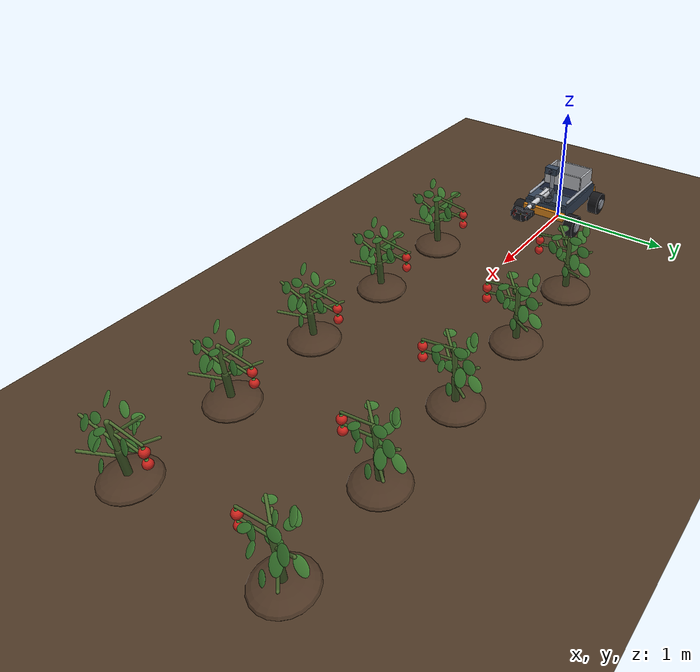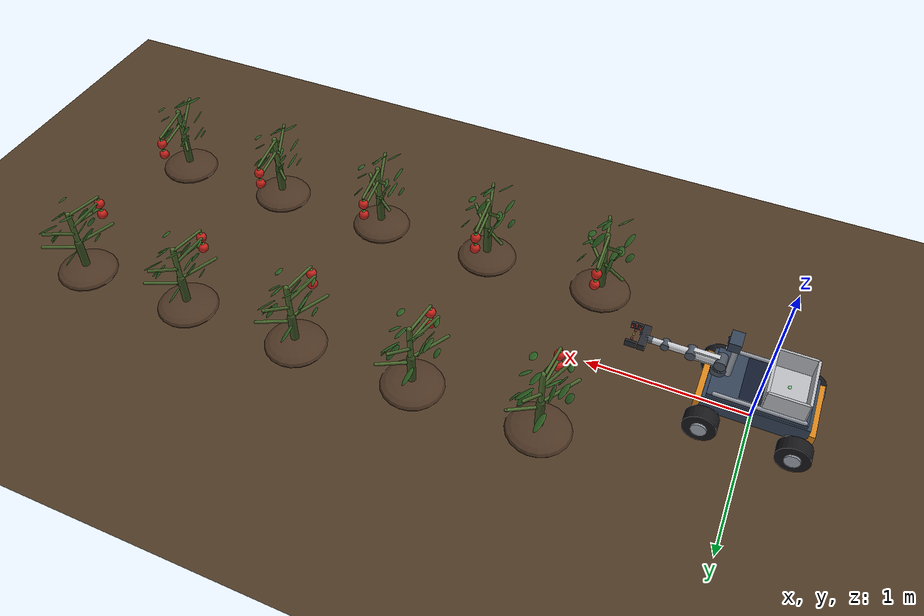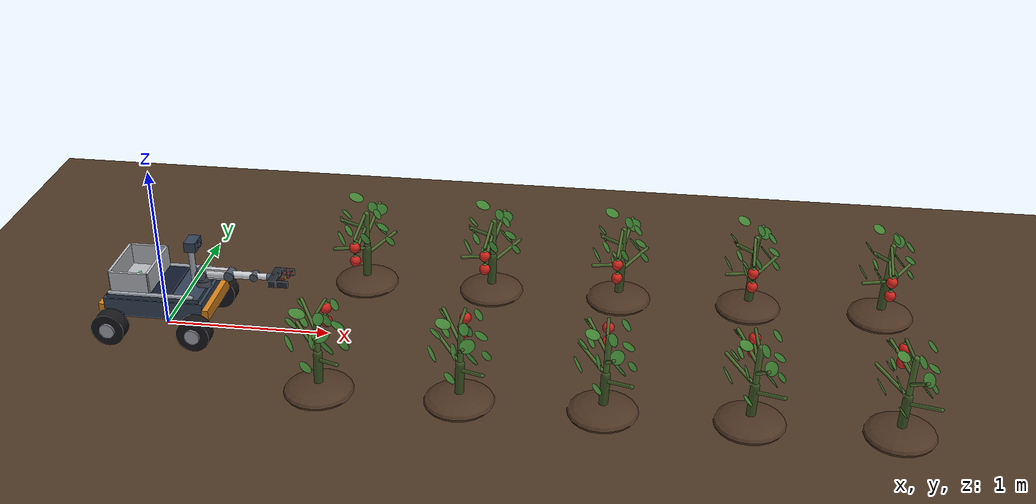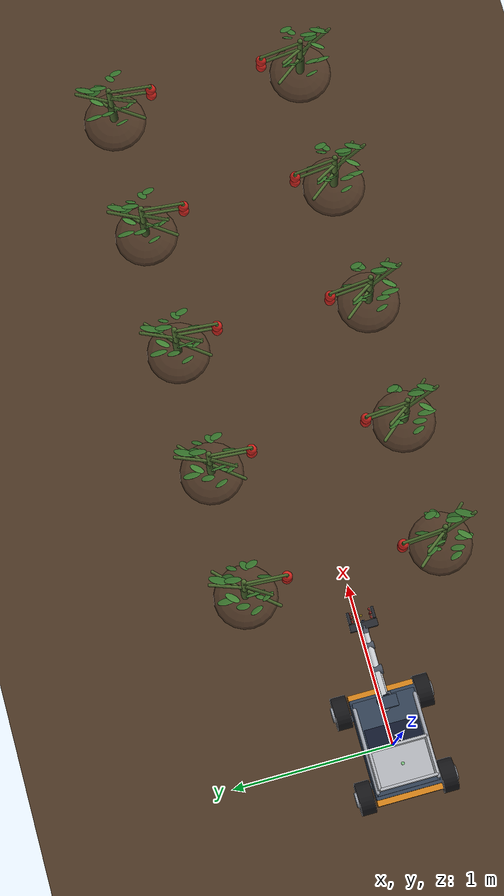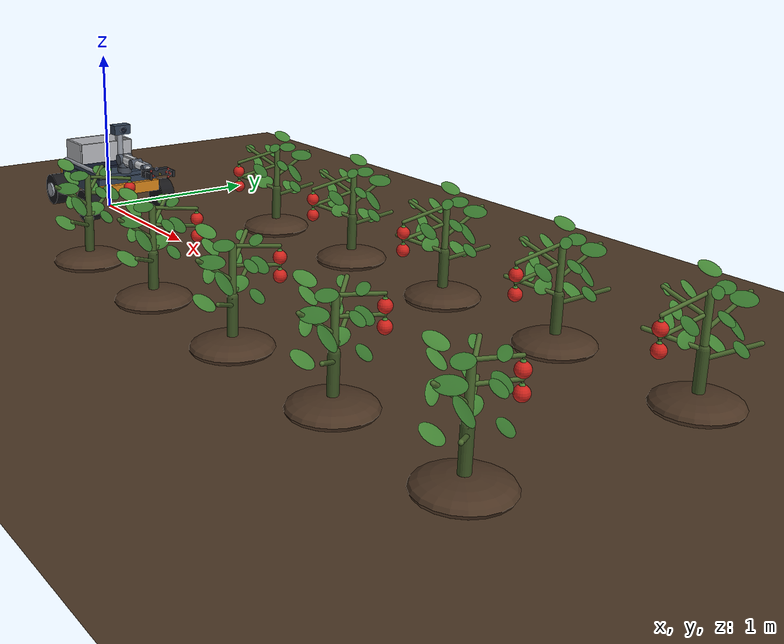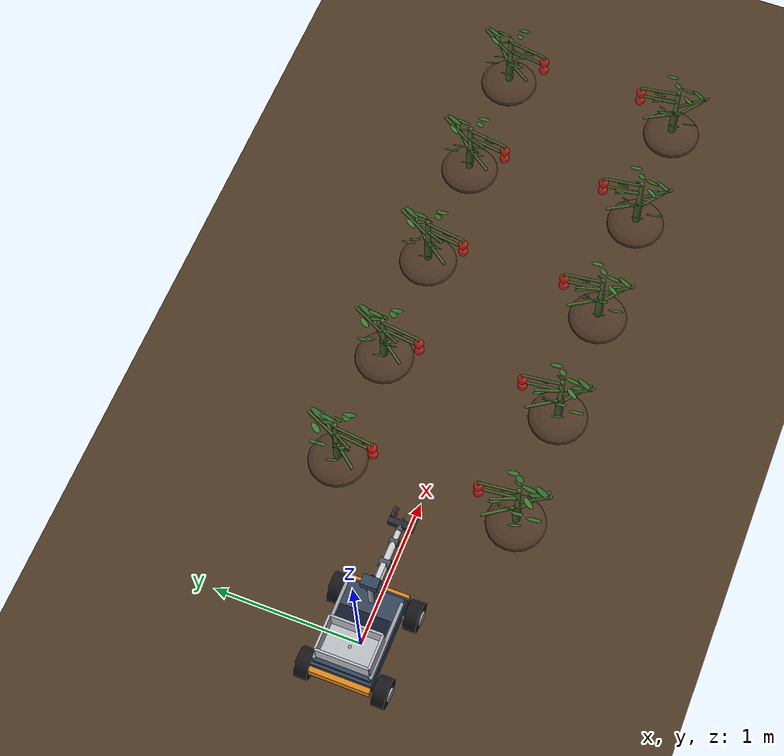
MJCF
<mujoco model="farm_harvest_rover">
  <compiler angle="radian" autolimits="true"/>
  <option timestep="0.001" integrator="implicitfast" gravity="0 0 -9.81"
          cone="pyramidal" solver="Newton" iterations="150" ls_iterations="50"/>
  <size njmax="800" nconmax="300"/>

  <visual>
    <global offwidth="1920" offheight="1080"/>
    <headlight ambient="0.45 0.45 0.45" diffuse="0.5 0.5 0.5" specular="0.2 0.2 0.2"/>
    <rgba haze="0.75 0.82 0.88 1"/>
    <quality shadowsize="4096" offsamples="8"/>
    <map znear="0.02" zfar="60" shadowclip="3"/>
  </visual>

  <asset>
    <texture type="skybox" builtin="gradient" rgb1="0.45 0.62 0.85" rgb2="0.85 0.91 0.97"
             width="512" height="512"/>
    <texture type="2d" name="soil_tex" builtin="checker" rgb1="0.31 0.225 0.15"
             rgb2="0.295 0.215 0.142" width="512" height="512" mark="random" markrgb="0.35 0.26 0.18"/>
    <material name="soil_mat" texture="soil_tex" texrepeat="260 170" specular="0.05" shininess="0.05"/>

    <texture type="2d" name="metal_tex" builtin="flat" rgb1="0.26 0.30 0.36"
             width="64" height="64"/>
    <material name="body_mat"   rgba="0.20 0.26 0.34 1" specular="0.55" shininess="0.55" reflectance="0.12"/>
    <material name="accent_mat" rgba="0.85 0.52 0.10 1" specular="0.4"  shininess="0.4"/>
    <material name="panel_mat"  rgba="0.07 0.10 0.18 1" specular="0.9"  shininess="0.9" reflectance="0.35"/>
    <material name="tire_mat"   rgba="0.09 0.09 0.10 1" specular="0.1"  shininess="0.1"/>
    <material name="hub_mat"    rgba="0.62 0.64 0.68 1" specular="0.8"  shininess="0.8" reflectance="0.25"/>
    <material name="arm_mat"    rgba="0.80 0.81 0.83 1" specular="0.7"  shininess="0.7" reflectance="0.2"/>
    <material name="joint_mat"  rgba="0.30 0.33 0.38 1" specular="0.6"  shininess="0.6"/>
    <material name="grip_mat"   rgba="0.15 0.16 0.18 1" specular="0.3"  shininess="0.3"/>
    <material name="pad_mat"    rgba="0.55 0.16 0.14 1" specular="0.15" shininess="0.15"/>
    <material name="crate_mat"  rgba="0.72 0.73 0.75 1" specular="0.35" shininess="0.35"/>
    <material name="lens_mat"   rgba="0.05 0.08 0.14 1" specular="1.0"  shininess="1.0" reflectance="0.5"/>

    <material name="stem_mat"   rgba="0.30 0.42 0.18 1" specular="0.12" shininess="0.2"/>
    <material name="stem_dark"  rgba="0.24 0.33 0.14 1" specular="0.1"  shininess="0.15"/>
    <material name="leaf_a_mat" rgba="0.20 0.44 0.16 1" specular="0.22" shininess="0.35"/>
    <material name="leaf_b_mat" rgba="0.26 0.52 0.20 1" specular="0.22" shininess="0.35"/>
    <material name="fruit_mat"  rgba="0.82 0.14 0.11 1" specular="0.62" shininess="0.75" reflectance="0.12"/>
    <material name="calyx_mat"  rgba="0.28 0.52 0.20 1" specular="0.2"  shininess="0.3"/>
    <material name="mound_mat"  rgba="0.30 0.21 0.14 1" specular="0.05" shininess="0.05"/>
  </asset>

  <default>
    <default class="wheel">
      <joint type="hinge" axis="0 1 0" damping="0.6" armature="0.02"/>
      <geom type="cylinder" size="0.10 0.045" euler="1.5708 0 0" material="tire_mat"
            friction="1.6 0.02 0.001" condim="4" contype="1" conaffinity="1"
            mass="0.9" priority="2" solref="0.010 1"/>
    </default>
    <default class="armlink">
      <joint type="hinge" damping="6.0" armature="0.02" frictionloss="0.2"/>
      <geom material="arm_mat" contype="0" conaffinity="0" density="600"/>
    </default>
    <default class="finger">
      <joint type="slide" damping="12.0" armature="0.005" frictionloss="0.4"/>
      <geom type="box" material="grip_mat" contype="1" conaffinity="1"
            friction="3.0 0.08 0.004" condim="4" priority="3" solref="0.008 1" density="900"/>
    </default>
    <!-- Stems collide only with the chassis (bit 2), never with fruit or wheels. -->
    <default class="stem">
      <geom type="capsule" material="stem_mat" contype="2" conaffinity="2" density="400"/>
    </default>
    <!-- Leaves are decorative only. -->
    <default class="leaf">
      <geom type="ellipsoid" material="leaf_a_mat" contype="0" conaffinity="0" density="100"/>
    </default>
    <default class="fruit">
      <geom type="sphere" material="fruit_mat" contype="1" conaffinity="1"
            friction="1.4 0.03 0.002" condim="4" solref="0.008 1"/>
    </default>
  </default>

  <worldbody>
    <light name="sun" directional="true" pos="2 -3 6" dir="-0.3 0.45 -1"
           diffuse="0.85 0.83 0.78" specular="0.25 0.25 0.25" castshadow="true"/>
    <light name="fill" directional="true" pos="-3 3 5" dir="0.4 -0.4 -1"
           diffuse="0.25 0.27 0.32" specular="0 0 0" castshadow="false"/>

    <geom name="ground" type="plane" size="12 8 0.1" material="soil_mat"
          friction="1.4 0.02 0.001" condim="4" contype="1" conaffinity="3"/>

    <!-- ==================== CROP ROWS ==================== -->
    <body name="plant_n0" pos="1.1 0.62 0">
      <geom class="stem" type="ellipsoid" size="0.20 0.20 0.055" pos="0 0 0.02" material="mound_mat" contype="0" conaffinity="0"/>
      <geom class="stem" size="0.026 0.020" fromto="0 0 0.03 0.01 0 0.26" material="stem_dark"/>
      <geom class="stem" size="0.017" fromto="0.01 0 0.26 0.02 0 0.50"/>
      <geom class="stem" size="0.010" fromto="0.01 0 0.220 0.160 0.160 0.300"/>
      <geom class="stem" size="0.010" fromto="0.01 0 0.260 -0.150 -0.180 0.340"/>
      <geom class="stem" size="0.010" fromto="0.01 0 0.340 0.060 0.200 0.480"/>
      <geom class="stem" size="0.010" fromto="0.01 0 0.400 -0.100 -0.140 0.520"/>
      <geom class="stem" size="0.009" fromto="0.01 0 0.500 0.000 -0.260 0.455"/>
      <geom class="stem" size="0.009" fromto="0.01 0 0.410 0.000 -0.260 0.365"/>
      <geom class="leaf" size="0.042 0.026 0.004" pos="0.150 0.045 0.295" euler="0.35 0.95 0.2" material="leaf_a_mat"/>
      <geom class="leaf" size="0.052 0.032 0.004" pos="-0.140 -0.035 0.335" euler="-0.25 1.0 -0.45" material="leaf_b_mat"/>
      <geom class="leaf" size="0.062 0.038 0.004" pos="0.075 0.140 0.465" euler="0.4 0.7 0.9" material="leaf_a_mat"/>
      <geom class="leaf" size="0.042 0.026 0.004" pos="-0.100 -0.115 0.505" euler="-0.5 0.8 -0.8" material="leaf_b_mat"/>
      <geom class="leaf" size="0.052 0.032 0.004" pos="0.035 -0.130 0.395" euler="0.2 1.1 0.5" material="leaf_a_mat"/>
      <geom class="leaf" size="0.062 0.038 0.004" pos="-0.028 0.125 0.245" euler="-0.3 0.9 1.2" material="leaf_b_mat"/>
      <geom class="leaf" size="0.042 0.026 0.004" pos="0.105 -0.070 0.540" euler="0.1 0.6 -1.1" material="leaf_a_mat"/>
      <geom class="leaf" size="0.052 0.032 0.004" pos="-0.062 0.090 0.565" euler="0.5 0.7 0.3" material="leaf_b_mat"/>
      <geom class="leaf" size="0.062 0.038 0.004" pos="0.085 0.085 0.360" euler="-0.4 0.85 0.65" material="leaf_a_mat"/>
      <geom class="leaf" size="0.042 0.026 0.004" pos="-0.080 -0.075 0.415" euler="0.45 1.05 -0.25" material="leaf_b_mat"/>
      <geom class="leaf" size="0.052 0.032 0.004" pos="0.045 0.060 0.520" euler="0.15 0.75 1.4" material="leaf_a_mat"/>
      <geom class="leaf" size="0.062 0.038 0.004" pos="-0.035 -0.055 0.300" euler="-0.2 1.15 -1.3" material="leaf_b_mat"/>
      <geom class="leaf" size="0.042 0.026 0.004" pos="0.125 -0.030 0.430" euler="0.3 0.65 0.05" material="leaf_a_mat"/>
      <geom class="leaf" size="0.052 0.032 0.004" pos="-0.115 0.040 0.470" euler="-0.35 0.9 0.95" material="leaf_b_mat"/>
    </body>
    <body name="plant_n1" pos="1.9 0.62 0">
      <geom class="stem" type="ellipsoid" size="0.20 0.20 0.055" pos="0 0 0.02" material="mound_mat" contype="0" conaffinity="0"/>
      <geom class="stem" size="0.026 0.020" fromto="0 0 0.03 0.01 0 0.26" material="stem_dark"/>
      <geom class="stem" size="0.017" fromto="0.01 0 0.26 0.02 0 0.50"/>
      <geom class="stem" size="0.010" fromto="0.01 0 0.220 0.160 0.160 0.300"/>
      <geom class="stem" size="0.010" fromto="0.01 0 0.260 -0.150 -0.180 0.340"/>
      <geom class="stem" size="0.010" fromto="0.01 0 0.340 0.060 0.200 0.480"/>
      <geom class="stem" size="0.010" fromto="0.01 0 0.400 -0.100 -0.140 0.520"/>
      <geom class="stem" size="0.009" fromto="0.01 0 0.500 0.000 -0.260 0.455"/>
      <geom class="stem" size="0.009" fromto="0.01 0 0.410 0.000 -0.260 0.365"/>
      <geom class="leaf" size="0.042 0.026 0.004" pos="0.150 0.045 0.295" euler="0.35 0.95 0.2" material="leaf_a_mat"/>
      <geom class="leaf" size="0.052 0.032 0.004" pos="-0.140 -0.035 0.335" euler="-0.25 1.0 -0.45" material="leaf_b_mat"/>
      <geom class="leaf" size="0.062 0.038 0.004" pos="0.075 0.140 0.465" euler="0.4 0.7 0.9" material="leaf_a_mat"/>
      <geom class="leaf" size="0.042 0.026 0.004" pos="-0.100 -0.115 0.505" euler="-0.5 0.8 -0.8" material="leaf_b_mat"/>
      <geom class="leaf" size="0.052 0.032 0.004" pos="0.035 -0.130 0.395" euler="0.2 1.1 0.5" material="leaf_a_mat"/>
      <geom class="leaf" size="0.062 0.038 0.004" pos="-0.028 0.125 0.245" euler="-0.3 0.9 1.2" material="leaf_b_mat"/>
      <geom class="leaf" size="0.042 0.026 0.004" pos="0.105 -0.070 0.540" euler="0.1 0.6 -1.1" material="leaf_a_mat"/>
      <geom class="leaf" size="0.052 0.032 0.004" pos="-0.062 0.090 0.565" euler="0.5 0.7 0.3" material="leaf_b_mat"/>
      <geom class="leaf" size="0.062 0.038 0.004" pos="0.085 0.085 0.360" euler="-0.4 0.85 0.65" material="leaf_a_mat"/>
      <geom class="leaf" size="0.042 0.026 0.004" pos="-0.080 -0.075 0.415" euler="0.45 1.05 -0.25" material="leaf_b_mat"/>
      <geom class="leaf" size="0.052 0.032 0.004" pos="0.045 0.060 0.520" euler="0.15 0.75 1.4" material="leaf_a_mat"/>
      <geom class="leaf" size="0.062 0.038 0.004" pos="-0.035 -0.055 0.300" euler="-0.2 1.15 -1.3" material="leaf_b_mat"/>
      <geom class="leaf" size="0.042 0.026 0.004" pos="0.125 -0.030 0.430" euler="0.3 0.65 0.05" material="leaf_a_mat"/>
      <geom class="leaf" size="0.052 0.032 0.004" pos="-0.115 0.040 0.470" euler="-0.35 0.9 0.95" material="leaf_b_mat"/>
    </body>
    <body name="plant_n2" pos="2.7 0.62 0">
      <geom class="stem" type="ellipsoid" size="0.20 0.20 0.055" pos="0 0 0.02" material="mound_mat" contype="0" conaffinity="0"/>
      <geom class="stem" size="0.026 0.020" fromto="0 0 0.03 0.01 0 0.26" material="stem_dark"/>
      <geom class="stem" size="0.017" fromto="0.01 0 0.26 0.02 0 0.50"/>
      <geom class="stem" size="0.010" fromto="0.01 0 0.220 0.160 0.160 0.300"/>
      <geom class="stem" size="0.010" fromto="0.01 0 0.260 -0.150 -0.180 0.340"/>
      <geom class="stem" size="0.010" fromto="0.01 0 0.340 0.060 0.200 0.480"/>
      <geom class="stem" size="0.010" fromto="0.01 0 0.400 -0.100 -0.140 0.520"/>
      <geom class="stem" size="0.009" fromto="0.01 0 0.500 0.000 -0.260 0.455"/>
      <geom class="stem" size="0.009" fromto="0.01 0 0.410 0.000 -0.260 0.365"/>
      <geom class="leaf" size="0.042 0.026 0.004" pos="0.150 0.045 0.295" euler="0.35 0.95 0.2" material="leaf_a_mat"/>
      <geom class="leaf" size="0.052 0.032 0.004" pos="-0.140 -0.035 0.335" euler="-0.25 1.0 -0.45" material="leaf_b_mat"/>
      <geom class="leaf" size="0.062 0.038 0.004" pos="0.075 0.140 0.465" euler="0.4 0.7 0.9" material="leaf_a_mat"/>
      <geom class="leaf" size="0.042 0.026 0.004" pos="-0.100 -0.115 0.505" euler="-0.5 0.8 -0.8" material="leaf_b_mat"/>
      <geom class="leaf" size="0.052 0.032 0.004" pos="0.035 -0.130 0.395" euler="0.2 1.1 0.5" material="leaf_a_mat"/>
      <geom class="leaf" size="0.062 0.038 0.004" pos="-0.028 0.125 0.245" euler="-0.3 0.9 1.2" material="leaf_b_mat"/>
      <geom class="leaf" size="0.042 0.026 0.004" pos="0.105 -0.070 0.540" euler="0.1 0.6 -1.1" material="leaf_a_mat"/>
      <geom class="leaf" size="0.052 0.032 0.004" pos="-0.062 0.090 0.565" euler="0.5 0.7 0.3" material="leaf_b_mat"/>
      <geom class="leaf" size="0.062 0.038 0.004" pos="0.085 0.085 0.360" euler="-0.4 0.85 0.65" material="leaf_a_mat"/>
      <geom class="leaf" size="0.042 0.026 0.004" pos="-0.080 -0.075 0.415" euler="0.45 1.05 -0.25" material="leaf_b_mat"/>
      <geom class="leaf" size="0.052 0.032 0.004" pos="0.045 0.060 0.520" euler="0.15 0.75 1.4" material="leaf_a_mat"/>
      <geom class="leaf" size="0.062 0.038 0.004" pos="-0.035 -0.055 0.300" euler="-0.2 1.15 -1.3" material="leaf_b_mat"/>
      <geom class="leaf" size="0.042 0.026 0.004" pos="0.125 -0.030 0.430" euler="0.3 0.65 0.05" material="leaf_a_mat"/>
      <geom class="leaf" size="0.052 0.032 0.004" pos="-0.115 0.040 0.470" euler="-0.35 0.9 0.95" material="leaf_b_mat"/>
    </body>
    <body name="plant_n3" pos="3.5 0.62 0">
      <geom class="stem" type="ellipsoid" size="0.20 0.20 0.055" pos="0 0 0.02" material="mound_mat" contype="0" conaffinity="0"/>
      <geom class="stem" size="0.026 0.020" fromto="0 0 0.03 0.01 0 0.26" material="stem_dark"/>
      <geom class="stem" size="0.017" fromto="0.01 0 0.26 0.02 0 0.50"/>
      <geom class="stem" size="0.010" fromto="0.01 0 0.220 0.160 0.160 0.300"/>
      <geom class="stem" size="0.010" fromto="0.01 0 0.260 -0.150 -0.180 0.340"/>
      <geom class="stem" size="0.010" fromto="0.01 0 0.340 0.060 0.200 0.480"/>
      <geom class="stem" size="0.010" fromto="0.01 0 0.400 -0.100 -0.140 0.520"/>
      <geom class="stem" size="0.009" fromto="0.01 0 0.500 0.000 -0.260 0.455"/>
      <geom class="stem" size="0.009" fromto="0.01 0 0.410 0.000 -0.260 0.365"/>
      <geom class="leaf" size="0.042 0.026 0.004" pos="0.150 0.045 0.295" euler="0.35 0.95 0.2" material="leaf_a_mat"/>
      <geom class="leaf" size="0.052 0.032 0.004" pos="-0.140 -0.035 0.335" euler="-0.25 1.0 -0.45" material="leaf_b_mat"/>
      <geom class="leaf" size="0.062 0.038 0.004" pos="0.075 0.140 0.465" euler="0.4 0.7 0.9" material="leaf_a_mat"/>
      <geom class="leaf" size="0.042 0.026 0.004" pos="-0.100 -0.115 0.505" euler="-0.5 0.8 -0.8" material="leaf_b_mat"/>
      <geom class="leaf" size="0.052 0.032 0.004" pos="0.035 -0.130 0.395" euler="0.2 1.1 0.5" material="leaf_a_mat"/>
      <geom class="leaf" size="0.062 0.038 0.004" pos="-0.028 0.125 0.245" euler="-0.3 0.9 1.2" material="leaf_b_mat"/>
      <geom class="leaf" size="0.042 0.026 0.004" pos="0.105 -0.070 0.540" euler="0.1 0.6 -1.1" material="leaf_a_mat"/>
      <geom class="leaf" size="0.052 0.032 0.004" pos="-0.062 0.090 0.565" euler="0.5 0.7 0.3" material="leaf_b_mat"/>
      <geom class="leaf" size="0.062 0.038 0.004" pos="0.085 0.085 0.360" euler="-0.4 0.85 0.65" material="leaf_a_mat"/>
      <geom class="leaf" size="0.042 0.026 0.004" pos="-0.080 -0.075 0.415" euler="0.45 1.05 -0.25" material="leaf_b_mat"/>
      <geom class="leaf" size="0.052 0.032 0.004" pos="0.045 0.060 0.520" euler="0.15 0.75 1.4" material="leaf_a_mat"/>
      <geom class="leaf" size="0.062 0.038 0.004" pos="-0.035 -0.055 0.300" euler="-0.2 1.15 -1.3" material="leaf_b_mat"/>
      <geom class="leaf" size="0.042 0.026 0.004" pos="0.125 -0.030 0.430" euler="0.3 0.65 0.05" material="leaf_a_mat"/>
      <geom class="leaf" size="0.052 0.032 0.004" pos="-0.115 0.040 0.470" euler="-0.35 0.9 0.95" material="leaf_b_mat"/>
    </body>
    <body name="plant_n4" pos="4.3 0.62 0">
      <geom class="stem" type="ellipsoid" size="0.20 0.20 0.055" pos="0 0 0.02" material="mound_mat" contype="0" conaffinity="0"/>
      <geom class="stem" size="0.026 0.020" fromto="0 0 0.03 0.01 0 0.26" material="stem_dark"/>
      <geom class="stem" size="0.017" fromto="0.01 0 0.26 0.02 0 0.50"/>
      <geom class="stem" size="0.010" fromto="0.01 0 0.220 0.160 0.160 0.300"/>
      <geom class="stem" size="0.010" fromto="0.01 0 0.260 -0.150 -0.180 0.340"/>
      <geom class="stem" size="0.010" fromto="0.01 0 0.340 0.060 0.200 0.480"/>
      <geom class="stem" size="0.010" fromto="0.01 0 0.400 -0.100 -0.140 0.520"/>
      <geom class="stem" size="0.009" fromto="0.01 0 0.500 0.000 -0.260 0.455"/>
      <geom class="stem" size="0.009" fromto="0.01 0 0.410 0.000 -0.260 0.365"/>
      <geom class="leaf" size="0.042 0.026 0.004" pos="0.150 0.045 0.295" euler="0.35 0.95 0.2" material="leaf_a_mat"/>
      <geom class="leaf" size="0.052 0.032 0.004" pos="-0.140 -0.035 0.335" euler="-0.25 1.0 -0.45" material="leaf_b_mat"/>
      <geom class="leaf" size="0.062 0.038 0.004" pos="0.075 0.140 0.465" euler="0.4 0.7 0.9" material="leaf_a_mat"/>
      <geom class="leaf" size="0.042 0.026 0.004" pos="-0.100 -0.115 0.505" euler="-0.5 0.8 -0.8" material="leaf_b_mat"/>
      <geom class="leaf" size="0.052 0.032 0.004" pos="0.035 -0.130 0.395" euler="0.2 1.1 0.5" material="leaf_a_mat"/>
      <geom class="leaf" size="0.062 0.038 0.004" pos="-0.028 0.125 0.245" euler="-0.3 0.9 1.2" material="leaf_b_mat"/>
      <geom class="leaf" size="0.042 0.026 0.004" pos="0.105 -0.070 0.540" euler="0.1 0.6 -1.1" material="leaf_a_mat"/>
      <geom class="leaf" size="0.052 0.032 0.004" pos="-0.062 0.090 0.565" euler="0.5 0.7 0.3" material="leaf_b_mat"/>
      <geom class="leaf" size="0.062 0.038 0.004" pos="0.085 0.085 0.360" euler="-0.4 0.85 0.65" material="leaf_a_mat"/>
      <geom class="leaf" size="0.042 0.026 0.004" pos="-0.080 -0.075 0.415" euler="0.45 1.05 -0.25" material="leaf_b_mat"/>
      <geom class="leaf" size="0.052 0.032 0.004" pos="0.045 0.060 0.520" euler="0.15 0.75 1.4" material="leaf_a_mat"/>
      <geom class="leaf" size="0.062 0.038 0.004" pos="-0.035 -0.055 0.300" euler="-0.2 1.15 -1.3" material="leaf_b_mat"/>
      <geom class="leaf" size="0.042 0.026 0.004" pos="0.125 -0.030 0.430" euler="0.3 0.65 0.05" material="leaf_a_mat"/>
      <geom class="leaf" size="0.052 0.032 0.004" pos="-0.115 0.040 0.470" euler="-0.35 0.9 0.95" material="leaf_b_mat"/>
    </body>
    <body name="plant_s0" pos="1.1 -0.62 0">
      <geom class="stem" type="ellipsoid" size="0.20 0.20 0.055" pos="0 0 0.02" material="mound_mat" contype="0" conaffinity="0"/>
      <geom class="stem" size="0.026 0.020" fromto="0 0 0.03 0.01 0 0.26" material="stem_dark"/>
      <geom class="stem" size="0.017" fromto="0.01 0 0.26 0.02 0 0.50"/>
      <geom class="stem" size="0.010" fromto="0.01 0 0.220 0.160 -0.160 0.300"/>
      <geom class="stem" size="0.010" fromto="0.01 0 0.260 -0.150 0.180 0.340"/>
      <geom class="stem" size="0.010" fromto="0.01 0 0.340 0.060 -0.200 0.480"/>
      <geom class="stem" size="0.010" fromto="0.01 0 0.400 -0.100 0.140 0.520"/>
      <geom class="stem" size="0.009" fromto="0.01 0 0.500 0.000 0.260 0.455"/>
      <geom class="stem" size="0.009" fromto="0.01 0 0.410 0.000 0.260 0.365"/>
      <geom class="leaf" size="0.042 0.026 0.004" pos="0.150 0.045 0.295" euler="0.35 0.95 0.2" material="leaf_a_mat"/>
      <geom class="leaf" size="0.052 0.032 0.004" pos="-0.140 -0.035 0.335" euler="-0.25 1.0 -0.45" material="leaf_b_mat"/>
      <geom class="leaf" size="0.062 0.038 0.004" pos="0.075 -0.140 0.465" euler="0.4 0.7 0.9" material="leaf_a_mat"/>
      <geom class="leaf" size="0.042 0.026 0.004" pos="-0.100 0.115 0.505" euler="-0.5 0.8 -0.8" material="leaf_b_mat"/>
      <geom class="leaf" size="0.052 0.032 0.004" pos="0.035 0.130 0.395" euler="0.2 1.1 0.5" material="leaf_a_mat"/>
      <geom class="leaf" size="0.062 0.038 0.004" pos="-0.028 -0.125 0.245" euler="-0.3 0.9 1.2" material="leaf_b_mat"/>
      <geom class="leaf" size="0.042 0.026 0.004" pos="0.105 0.070 0.540" euler="0.1 0.6 -1.1" material="leaf_a_mat"/>
      <geom class="leaf" size="0.052 0.032 0.004" pos="-0.062 -0.090 0.565" euler="0.5 0.7 0.3" material="leaf_b_mat"/>
      <geom class="leaf" size="0.062 0.038 0.004" pos="0.085 -0.085 0.360" euler="-0.4 0.85 0.65" material="leaf_a_mat"/>
      <geom class="leaf" size="0.042 0.026 0.004" pos="-0.080 0.075 0.415" euler="0.45 1.05 -0.25" material="leaf_b_mat"/>
      <geom class="leaf" size="0.052 0.032 0.004" pos="0.045 -0.060 0.520" euler="0.15 0.75 1.4" material="leaf_a_mat"/>
      <geom class="leaf" size="0.062 0.038 0.004" pos="-0.035 0.055 0.300" euler="-0.2 1.15 -1.3" material="leaf_b_mat"/>
      <geom class="leaf" size="0.042 0.026 0.004" pos="0.125 0.030 0.430" euler="0.3 0.65 0.05" material="leaf_a_mat"/>
      <geom class="leaf" size="0.052 0.032 0.004" pos="-0.115 -0.040 0.470" euler="-0.35 0.9 0.95" material="leaf_b_mat"/>
    </body>
    <body name="plant_s1" pos="1.9 -0.62 0">
      <geom class="stem" type="ellipsoid" size="0.20 0.20 0.055" pos="0 0 0.02" material="mound_mat" contype="0" conaffinity="0"/>
      <geom class="stem" size="0.026 0.020" fromto="0 0 0.03 0.01 0 0.26" material="stem_dark"/>
      <geom class="stem" size="0.017" fromto="0.01 0 0.26 0.02 0 0.50"/>
      <geom class="stem" size="0.010" fromto="0.01 0 0.220 0.160 -0.160 0.300"/>
      <geom class="stem" size="0.010" fromto="0.01 0 0.260 -0.150 0.180 0.340"/>
      <geom class="stem" size="0.010" fromto="0.01 0 0.340 0.060 -0.200 0.480"/>
      <geom class="stem" size="0.010" fromto="0.01 0 0.400 -0.100 0.140 0.520"/>
      <geom class="stem" size="0.009" fromto="0.01 0 0.500 0.000 0.260 0.455"/>
      <geom class="stem" size="0.009" fromto="0.01 0 0.410 0.000 0.260 0.365"/>
      <geom class="leaf" size="0.042 0.026 0.004" pos="0.150 0.045 0.295" euler="0.35 0.95 0.2" material="leaf_a_mat"/>
      <geom class="leaf" size="0.052 0.032 0.004" pos="-0.140 -0.035 0.335" euler="-0.25 1.0 -0.45" material="leaf_b_mat"/>
      <geom class="leaf" size="0.062 0.038 0.004" pos="0.075 -0.140 0.465" euler="0.4 0.7 0.9" material="leaf_a_mat"/>
      <geom class="leaf" size="0.042 0.026 0.004" pos="-0.100 0.115 0.505" euler="-0.5 0.8 -0.8" material="leaf_b_mat"/>
      <geom class="leaf" size="0.052 0.032 0.004" pos="0.035 0.130 0.395" euler="0.2 1.1 0.5" material="leaf_a_mat"/>
      <geom class="leaf" size="0.062 0.038 0.004" pos="-0.028 -0.125 0.245" euler="-0.3 0.9 1.2" material="leaf_b_mat"/>
      <geom class="leaf" size="0.042 0.026 0.004" pos="0.105 0.070 0.540" euler="0.1 0.6 -1.1" material="leaf_a_mat"/>
      <geom class="leaf" size="0.052 0.032 0.004" pos="-0.062 -0.090 0.565" euler="0.5 0.7 0.3" material="leaf_b_mat"/>
      <geom class="leaf" size="0.062 0.038 0.004" pos="0.085 -0.085 0.360" euler="-0.4 0.85 0.65" material="leaf_a_mat"/>
      <geom class="leaf" size="0.042 0.026 0.004" pos="-0.080 0.075 0.415" euler="0.45 1.05 -0.25" material="leaf_b_mat"/>
      <geom class="leaf" size="0.052 0.032 0.004" pos="0.045 -0.060 0.520" euler="0.15 0.75 1.4" material="leaf_a_mat"/>
      <geom class="leaf" size="0.062 0.038 0.004" pos="-0.035 0.055 0.300" euler="-0.2 1.15 -1.3" material="leaf_b_mat"/>
      <geom class="leaf" size="0.042 0.026 0.004" pos="0.125 0.030 0.430" euler="0.3 0.65 0.05" material="leaf_a_mat"/>
      <geom class="leaf" size="0.052 0.032 0.004" pos="-0.115 -0.040 0.470" euler="-0.35 0.9 0.95" material="leaf_b_mat"/>
    </body>
    <body name="plant_s2" pos="2.7 -0.62 0">
      <geom class="stem" type="ellipsoid" size="0.20 0.20 0.055" pos="0 0 0.02" material="mound_mat" contype="0" conaffinity="0"/>
      <geom class="stem" size="0.026 0.020" fromto="0 0 0.03 0.01 0 0.26" material="stem_dark"/>
      <geom class="stem" size="0.017" fromto="0.01 0 0.26 0.02 0 0.50"/>
      <geom class="stem" size="0.010" fromto="0.01 0 0.220 0.160 -0.160 0.300"/>
      <geom class="stem" size="0.010" fromto="0.01 0 0.260 -0.150 0.180 0.340"/>
      <geom class="stem" size="0.010" fromto="0.01 0 0.340 0.060 -0.200 0.480"/>
      <geom class="stem" size="0.010" fromto="0.01 0 0.400 -0.100 0.140 0.520"/>
      <geom class="stem" size="0.009" fromto="0.01 0 0.500 0.000 0.260 0.455"/>
      <geom class="stem" size="0.009" fromto="0.01 0 0.410 0.000 0.260 0.365"/>
      <geom class="leaf" size="0.042 0.026 0.004" pos="0.150 0.045 0.295" euler="0.35 0.95 0.2" material="leaf_a_mat"/>
      <geom class="leaf" size="0.052 0.032 0.004" pos="-0.140 -0.035 0.335" euler="-0.25 1.0 -0.45" material="leaf_b_mat"/>
      <geom class="leaf" size="0.062 0.038 0.004" pos="0.075 -0.140 0.465" euler="0.4 0.7 0.9" material="leaf_a_mat"/>
      <geom class="leaf" size="0.042 0.026 0.004" pos="-0.100 0.115 0.505" euler="-0.5 0.8 -0.8" material="leaf_b_mat"/>
      <geom class="leaf" size="0.052 0.032 0.004" pos="0.035 0.130 0.395" euler="0.2 1.1 0.5" material="leaf_a_mat"/>
      <geom class="leaf" size="0.062 0.038 0.004" pos="-0.028 -0.125 0.245" euler="-0.3 0.9 1.2" material="leaf_b_mat"/>
      <geom class="leaf" size="0.042 0.026 0.004" pos="0.105 0.070 0.540" euler="0.1 0.6 -1.1" material="leaf_a_mat"/>
      <geom class="leaf" size="0.052 0.032 0.004" pos="-0.062 -0.090 0.565" euler="0.5 0.7 0.3" material="leaf_b_mat"/>
      <geom class="leaf" size="0.062 0.038 0.004" pos="0.085 -0.085 0.360" euler="-0.4 0.85 0.65" material="leaf_a_mat"/>
      <geom class="leaf" size="0.042 0.026 0.004" pos="-0.080 0.075 0.415" euler="0.45 1.05 -0.25" material="leaf_b_mat"/>
      <geom class="leaf" size="0.052 0.032 0.004" pos="0.045 -0.060 0.520" euler="0.15 0.75 1.4" material="leaf_a_mat"/>
      <geom class="leaf" size="0.062 0.038 0.004" pos="-0.035 0.055 0.300" euler="-0.2 1.15 -1.3" material="leaf_b_mat"/>
      <geom class="leaf" size="0.042 0.026 0.004" pos="0.125 0.030 0.430" euler="0.3 0.65 0.05" material="leaf_a_mat"/>
      <geom class="leaf" size="0.052 0.032 0.004" pos="-0.115 -0.040 0.470" euler="-0.35 0.9 0.95" material="leaf_b_mat"/>
    </body>
    <body name="plant_s3" pos="3.5 -0.62 0">
      <geom class="stem" type="ellipsoid" size="0.20 0.20 0.055" pos="0 0 0.02" material="mound_mat" contype="0" conaffinity="0"/>
      <geom class="stem" size="0.026 0.020" fromto="0 0 0.03 0.01 0 0.26" material="stem_dark"/>
      <geom class="stem" size="0.017" fromto="0.01 0 0.26 0.02 0 0.50"/>
      <geom class="stem" size="0.010" fromto="0.01 0 0.220 0.160 -0.160 0.300"/>
      <geom class="stem" size="0.010" fromto="0.01 0 0.260 -0.150 0.180 0.340"/>
      <geom class="stem" size="0.010" fromto="0.01 0 0.340 0.060 -0.200 0.480"/>
      <geom class="stem" size="0.010" fromto="0.01 0 0.400 -0.100 0.140 0.520"/>
      <geom class="stem" size="0.009" fromto="0.01 0 0.500 0.000 0.260 0.455"/>
      <geom class="stem" size="0.009" fromto="0.01 0 0.410 0.000 0.260 0.365"/>
      <geom class="leaf" size="0.042 0.026 0.004" pos="0.150 0.045 0.295" euler="0.35 0.95 0.2" material="leaf_a_mat"/>
      <geom class="leaf" size="0.052 0.032 0.004" pos="-0.140 -0.035 0.335" euler="-0.25 1.0 -0.45" material="leaf_b_mat"/>
      <geom class="leaf" size="0.062 0.038 0.004" pos="0.075 -0.140 0.465" euler="0.4 0.7 0.9" material="leaf_a_mat"/>
      <geom class="leaf" size="0.042 0.026 0.004" pos="-0.100 0.115 0.505" euler="-0.5 0.8 -0.8" material="leaf_b_mat"/>
      <geom class="leaf" size="0.052 0.032 0.004" pos="0.035 0.130 0.395" euler="0.2 1.1 0.5" material="leaf_a_mat"/>
      <geom class="leaf" size="0.062 0.038 0.004" pos="-0.028 -0.125 0.245" euler="-0.3 0.9 1.2" material="leaf_b_mat"/>
      <geom class="leaf" size="0.042 0.026 0.004" pos="0.105 0.070 0.540" euler="0.1 0.6 -1.1" material="leaf_a_mat"/>
      <geom class="leaf" size="0.052 0.032 0.004" pos="-0.062 -0.090 0.565" euler="0.5 0.7 0.3" material="leaf_b_mat"/>
      <geom class="leaf" size="0.062 0.038 0.004" pos="0.085 -0.085 0.360" euler="-0.4 0.85 0.65" material="leaf_a_mat"/>
      <geom class="leaf" size="0.042 0.026 0.004" pos="-0.080 0.075 0.415" euler="0.45 1.05 -0.25" material="leaf_b_mat"/>
      <geom class="leaf" size="0.052 0.032 0.004" pos="0.045 -0.060 0.520" euler="0.15 0.75 1.4" material="leaf_a_mat"/>
      <geom class="leaf" size="0.062 0.038 0.004" pos="-0.035 0.055 0.300" euler="-0.2 1.15 -1.3" material="leaf_b_mat"/>
      <geom class="leaf" size="0.042 0.026 0.004" pos="0.125 0.030 0.430" euler="0.3 0.65 0.05" material="leaf_a_mat"/>
      <geom class="leaf" size="0.052 0.032 0.004" pos="-0.115 -0.040 0.470" euler="-0.35 0.9 0.95" material="leaf_b_mat"/>
    </body>
    <body name="plant_s4" pos="4.3 -0.62 0">
      <geom class="stem" type="ellipsoid" size="0.20 0.20 0.055" pos="0 0 0.02" material="mound_mat" contype="0" conaffinity="0"/>
      <geom class="stem" size="0.026 0.020" fromto="0 0 0.03 0.01 0 0.26" material="stem_dark"/>
      <geom class="stem" size="0.017" fromto="0.01 0 0.26 0.02 0 0.50"/>
      <geom class="stem" size="0.010" fromto="0.01 0 0.220 0.160 -0.160 0.300"/>
      <geom class="stem" size="0.010" fromto="0.01 0 0.260 -0.150 0.180 0.340"/>
      <geom class="stem" size="0.010" fromto="0.01 0 0.340 0.060 -0.200 0.480"/>
      <geom class="stem" size="0.010" fromto="0.01 0 0.400 -0.100 0.140 0.520"/>
      <geom class="stem" size="0.009" fromto="0.01 0 0.500 0.000 0.260 0.455"/>
      <geom class="stem" size="0.009" fromto="0.01 0 0.410 0.000 0.260 0.365"/>
      <geom class="leaf" size="0.042 0.026 0.004" pos="0.150 0.045 0.295" euler="0.35 0.95 0.2" material="leaf_a_mat"/>
      <geom class="leaf" size="0.052 0.032 0.004" pos="-0.140 -0.035 0.335" euler="-0.25 1.0 -0.45" material="leaf_b_mat"/>
      <geom class="leaf" size="0.062 0.038 0.004" pos="0.075 -0.140 0.465" euler="0.4 0.7 0.9" material="leaf_a_mat"/>
      <geom class="leaf" size="0.042 0.026 0.004" pos="-0.100 0.115 0.505" euler="-0.5 0.8 -0.8" material="leaf_b_mat"/>
      <geom class="leaf" size="0.052 0.032 0.004" pos="0.035 0.130 0.395" euler="0.2 1.1 0.5" material="leaf_a_mat"/>
      <geom class="leaf" size="0.062 0.038 0.004" pos="-0.028 -0.125 0.245" euler="-0.3 0.9 1.2" material="leaf_b_mat"/>
      <geom class="leaf" size="0.042 0.026 0.004" pos="0.105 0.070 0.540" euler="0.1 0.6 -1.1" material="leaf_a_mat"/>
      <geom class="leaf" size="0.052 0.032 0.004" pos="-0.062 -0.090 0.565" euler="0.5 0.7 0.3" material="leaf_b_mat"/>
      <geom class="leaf" size="0.062 0.038 0.004" pos="0.085 -0.085 0.360" euler="-0.4 0.85 0.65" material="leaf_a_mat"/>
      <geom class="leaf" size="0.042 0.026 0.004" pos="-0.080 0.075 0.415" euler="0.45 1.05 -0.25" material="leaf_b_mat"/>
      <geom class="leaf" size="0.052 0.032 0.004" pos="0.045 -0.060 0.520" euler="0.15 0.75 1.4" material="leaf_a_mat"/>
      <geom class="leaf" size="0.062 0.038 0.004" pos="-0.035 0.055 0.300" euler="-0.2 1.15 -1.3" material="leaf_b_mat"/>
      <geom class="leaf" size="0.042 0.026 0.004" pos="0.125 0.030 0.430" euler="0.3 0.65 0.05" material="leaf_a_mat"/>
      <geom class="leaf" size="0.052 0.032 0.004" pos="-0.115 -0.040 0.470" euler="-0.35 0.9 0.95" material="leaf_b_mat"/>
    </body>

    <!-- ==================== FRUIT ==================== -->
    <body name="fruit_n0_0" pos="1.1000 0.3600 0.4000">
      <freejoint name="fruit_n0_0_free"/>
      <geom class="fruit" size="0.033" mass="0.120"/>
      <geom type="sphere" size="0.012" pos="0 0 0.0290"
            material="calyx_mat" contype="0" conaffinity="0" mass="0.001"/>
      <geom type="capsule" size="0.005"
            fromto="0 0 0.0330 0 0 0.0530"
            material="stem_dark" contype="0" conaffinity="0" mass="0.001"/>
      <site name="fruit_n0_0_site" pos="0 0 0" size="0.004" rgba="1 1 0 0.2"/>
    </body>
    <body name="fruit_n0_1" pos="1.1000 0.3600 0.3100">
      <freejoint name="fruit_n0_1_free"/>
      <geom class="fruit" size="0.033" mass="0.120"/>
      <geom type="sphere" size="0.012" pos="0 0 0.0290"
            material="calyx_mat" contype="0" conaffinity="0" mass="0.001"/>
      <geom type="capsule" size="0.005"
            fromto="0 0 0.0330 0 0 0.0530"
            material="stem_dark" contype="0" conaffinity="0" mass="0.001"/>
      <site name="fruit_n0_1_site" pos="0 0 0" size="0.004" rgba="1 1 0 0.2"/>
    </body>
    <body name="fruit_n1_0" pos="1.9000 0.3600 0.4000">
      <freejoint name="fruit_n1_0_free"/>
      <geom class="fruit" size="0.033" mass="0.120"/>
      <geom type="sphere" size="0.012" pos="0 0 0.0290"
            material="calyx_mat" contype="0" conaffinity="0" mass="0.001"/>
      <geom type="capsule" size="0.005"
            fromto="0 0 0.0330 0 0 0.0530"
            material="stem_dark" contype="0" conaffinity="0" mass="0.001"/>
      <site name="fruit_n1_0_site" pos="0 0 0" size="0.004" rgba="1 1 0 0.2"/>
    </body>
    <body name="fruit_n1_1" pos="1.9000 0.3600 0.3100">
      <freejoint name="fruit_n1_1_free"/>
      <geom class="fruit" size="0.033" mass="0.120"/>
      <geom type="sphere" size="0.012" pos="0 0 0.0290"
            material="calyx_mat" contype="0" conaffinity="0" mass="0.001"/>
      <geom type="capsule" size="0.005"
            fromto="0 0 0.0330 0 0 0.0530"
            material="stem_dark" contype="0" conaffinity="0" mass="0.001"/>
      <site name="fruit_n1_1_site" pos="0 0 0" size="0.004" rgba="1 1 0 0.2"/>
    </body>
    <body name="fruit_n2_0" pos="2.7000 0.3600 0.4000">
      <freejoint name="fruit_n2_0_free"/>
      <geom class="fruit" size="0.033" mass="0.120"/>
      <geom type="sphere" size="0.012" pos="0 0 0.0290"
            material="calyx_mat" contype="0" conaffinity="0" mass="0.001"/>
      <geom type="capsule" size="0.005"
            fromto="0 0 0.0330 0 0 0.0530"
            material="stem_dark" contype="0" conaffinity="0" mass="0.001"/>
      <site name="fruit_n2_0_site" pos="0 0 0" size="0.004" rgba="1 1 0 0.2"/>
    </body>
    <body name="fruit_n2_1" pos="2.7000 0.3600 0.3100">
      <freejoint name="fruit_n2_1_free"/>
      <geom class="fruit" size="0.033" mass="0.120"/>
      <geom type="sphere" size="0.012" pos="0 0 0.0290"
            material="calyx_mat" contype="0" conaffinity="0" mass="0.001"/>
      <geom type="capsule" size="0.005"
            fromto="0 0 0.0330 0 0 0.0530"
            material="stem_dark" contype="0" conaffinity="0" mass="0.001"/>
      <site name="fruit_n2_1_site" pos="0 0 0" size="0.004" rgba="1 1 0 0.2"/>
    </body>
    <body name="fruit_n3_0" pos="3.5000 0.3600 0.4000">
      <freejoint name="fruit_n3_0_free"/>
      <geom class="fruit" size="0.033" mass="0.120"/>
      <geom type="sphere" size="0.012" pos="0 0 0.0290"
            material="calyx_mat" contype="0" conaffinity="0" mass="0.001"/>
      <geom type="capsule" size="0.005"
            fromto="0 0 0.0330 0 0 0.0530"
            material="stem_dark" contype="0" conaffinity="0" mass="0.001"/>
      <site name="fruit_n3_0_site" pos="0 0 0" size="0.004" rgba="1 1 0 0.2"/>
    </body>
    <body name="fruit_n3_1" pos="3.5000 0.3600 0.3100">
      <freejoint name="fruit_n3_1_free"/>
      <geom class="fruit" size="0.033" mass="0.120"/>
      <geom type="sphere" size="0.012" pos="0 0 0.0290"
            material="calyx_mat" contype="0" conaffinity="0" mass="0.001"/>
      <geom type="capsule" size="0.005"
            fromto="0 0 0.0330 0 0 0.0530"
            material="stem_dark" contype="0" conaffinity="0" mass="0.001"/>
      <site name="fruit_n3_1_site" pos="0 0 0" size="0.004" rgba="1 1 0 0.2"/>
    </body>
    <body name="fruit_n4_0" pos="4.3000 0.3600 0.4000">
      <freejoint name="fruit_n4_0_free"/>
      <geom class="fruit" size="0.033" mass="0.120"/>
      <geom type="sphere" size="0.012" pos="0 0 0.0290"
            material="calyx_mat" contype="0" conaffinity="0" mass="0.001"/>
      <geom type="capsule" size="0.005"
            fromto="0 0 0.0330 0 0 0.0530"
            material="stem_dark" contype="0" conaffinity="0" mass="0.001"/>
      <site name="fruit_n4_0_site" pos="0 0 0" size="0.004" rgba="1 1 0 0.2"/>
    </body>
    <body name="fruit_n4_1" pos="4.3000 0.3600 0.3100">
      <freejoint name="fruit_n4_1_free"/>
      <geom class="fruit" size="0.033" mass="0.120"/>
      <geom type="sphere" size="0.012" pos="0 0 0.0290"
            material="calyx_mat" contype="0" conaffinity="0" mass="0.001"/>
      <geom type="capsule" size="0.005"
            fromto="0 0 0.0330 0 0 0.0530"
            material="stem_dark" contype="0" conaffinity="0" mass="0.001"/>
      <site name="fruit_n4_1_site" pos="0 0 0" size="0.004" rgba="1 1 0 0.2"/>
    </body>
    <body name="fruit_s0_0" pos="1.1000 -0.3600 0.4000">
      <freejoint name="fruit_s0_0_free"/>
      <geom class="fruit" size="0.033" mass="0.120"/>
      <geom type="sphere" size="0.012" pos="0 0 0.0290"
            material="calyx_mat" contype="0" conaffinity="0" mass="0.001"/>
      <geom type="capsule" size="0.005"
            fromto="0 0 0.0330 0 0 0.0530"
            material="stem_dark" contype="0" conaffinity="0" mass="0.001"/>
      <site name="fruit_s0_0_site" pos="0 0 0" size="0.004" rgba="1 1 0 0.2"/>
    </body>
    <body name="fruit_s0_1" pos="1.1000 -0.3600 0.3100">
      <freejoint name="fruit_s0_1_free"/>
      <geom class="fruit" size="0.033" mass="0.120"/>
      <geom type="sphere" size="0.012" pos="0 0 0.0290"
            material="calyx_mat" contype="0" conaffinity="0" mass="0.001"/>
      <geom type="capsule" size="0.005"
            fromto="0 0 0.0330 0 0 0.0530"
            material="stem_dark" contype="0" conaffinity="0" mass="0.001"/>
      <site name="fruit_s0_1_site" pos="0 0 0" size="0.004" rgba="1 1 0 0.2"/>
    </body>
    <body name="fruit_s1_0" pos="1.9000 -0.3600 0.4000">
      <freejoint name="fruit_s1_0_free"/>
      <geom class="fruit" size="0.033" mass="0.120"/>
      <geom type="sphere" size="0.012" pos="0 0 0.0290"
            material="calyx_mat" contype="0" conaffinity="0" mass="0.001"/>
      <geom type="capsule" size="0.005"
            fromto="0 0 0.0330 0 0 0.0530"
            material="stem_dark" contype="0" conaffinity="0" mass="0.001"/>
      <site name="fruit_s1_0_site" pos="0 0 0" size="0.004" rgba="1 1 0 0.2"/>
    </body>
    <body name="fruit_s1_1" pos="1.9000 -0.3600 0.3100">
      <freejoint name="fruit_s1_1_free"/>
      <geom class="fruit" size="0.033" mass="0.120"/>
      <geom type="sphere" size="0.012" pos="0 0 0.0290"
            material="calyx_mat" contype="0" conaffinity="0" mass="0.001"/>
      <geom type="capsule" size="0.005"
            fromto="0 0 0.0330 0 0 0.0530"
            material="stem_dark" contype="0" conaffinity="0" mass="0.001"/>
      <site name="fruit_s1_1_site" pos="0 0 0" size="0.004" rgba="1 1 0 0.2"/>
    </body>
    <body name="fruit_s2_0" pos="2.7000 -0.3600 0.4000">
      <freejoint name="fruit_s2_0_free"/>
      <geom class="fruit" size="0.033" mass="0.120"/>
      <geom type="sphere" size="0.012" pos="0 0 0.0290"
            material="calyx_mat" contype="0" conaffinity="0" mass="0.001"/>
      <geom type="capsule" size="0.005"
            fromto="0 0 0.0330 0 0 0.0530"
            material="stem_dark" contype="0" conaffinity="0" mass="0.001"/>
      <site name="fruit_s2_0_site" pos="0 0 0" size="0.004" rgba="1 1 0 0.2"/>
    </body>
    <body name="fruit_s2_1" pos="2.7000 -0.3600 0.3100">
      <freejoint name="fruit_s2_1_free"/>
      <geom class="fruit" size="0.033" mass="0.120"/>
      <geom type="sphere" size="0.012" pos="0 0 0.0290"
            material="calyx_mat" contype="0" conaffinity="0" mass="0.001"/>
      <geom type="capsule" size="0.005"
            fromto="0 0 0.0330 0 0 0.0530"
            material="stem_dark" contype="0" conaffinity="0" mass="0.001"/>
      <site name="fruit_s2_1_site" pos="0 0 0" size="0.004" rgba="1 1 0 0.2"/>
    </body>
    <body name="fruit_s3_0" pos="3.5000 -0.3600 0.4000">
      <freejoint name="fruit_s3_0_free"/>
      <geom class="fruit" size="0.033" mass="0.120"/>
      <geom type="sphere" size="0.012" pos="0 0 0.0290"
            material="calyx_mat" contype="0" conaffinity="0" mass="0.001"/>
      <geom type="capsule" size="0.005"
            fromto="0 0 0.0330 0 0 0.0530"
            material="stem_dark" contype="0" conaffinity="0" mass="0.001"/>
      <site name="fruit_s3_0_site" pos="0 0 0" size="0.004" rgba="1 1 0 0.2"/>
    </body>
    <body name="fruit_s3_1" pos="3.5000 -0.3600 0.3100">
      <freejoint name="fruit_s3_1_free"/>
      <geom class="fruit" size="0.033" mass="0.120"/>
      <geom type="sphere" size="0.012" pos="0 0 0.0290"
            material="calyx_mat" contype="0" conaffinity="0" mass="0.001"/>
      <geom type="capsule" size="0.005"
            fromto="0 0 0.0330 0 0 0.0530"
            material="stem_dark" contype="0" conaffinity="0" mass="0.001"/>
      <site name="fruit_s3_1_site" pos="0 0 0" size="0.004" rgba="1 1 0 0.2"/>
    </body>
    <body name="fruit_s4_0" pos="4.3000 -0.3600 0.4000">
      <freejoint name="fruit_s4_0_free"/>
      <geom class="fruit" size="0.033" mass="0.120"/>
      <geom type="sphere" size="0.012" pos="0 0 0.0290"
            material="calyx_mat" contype="0" conaffinity="0" mass="0.001"/>
      <geom type="capsule" size="0.005"
            fromto="0 0 0.0330 0 0 0.0530"
            material="stem_dark" contype="0" conaffinity="0" mass="0.001"/>
      <site name="fruit_s4_0_site" pos="0 0 0" size="0.004" rgba="1 1 0 0.2"/>
    </body>
    <body name="fruit_s4_1" pos="4.3000 -0.3600 0.3100">
      <freejoint name="fruit_s4_1_free"/>
      <geom class="fruit" size="0.033" mass="0.120"/>
      <geom type="sphere" size="0.012" pos="0 0 0.0290"
            material="calyx_mat" contype="0" conaffinity="0" mass="0.001"/>
      <geom type="capsule" size="0.005"
            fromto="0 0 0.0330 0 0 0.0530"
            material="stem_dark" contype="0" conaffinity="0" mass="0.001"/>
      <site name="fruit_s4_1_site" pos="0 0 0" size="0.004" rgba="1 1 0 0.2"/>
    </body>

    <!-- ==================== ROVER ==================== -->
    <body name="chassis" pos="0 0 0.10">
      <freejoint name="chassis_free"/>
      <inertial pos="0 -0.0 0.08" mass="14.0" diaginertia="0.45 0.60 0.75"/>

      <!-- main hull -->
      <geom name="hull" type="box" size="0.30 0.20 0.055" pos="0 0 0.105"
            material="body_mat" contype="2" conaffinity="3" friction="0.5 0.01 0.001"/>
      <geom name="skid_plate" type="box" size="0.26 0.18 0.012" pos="0 0 0.045"
            material="panel_mat" contype="2" conaffinity="3"/>
      <geom name="deck" type="box" size="0.28 0.19 0.012" pos="0 0 0.172"
            material="body_mat" contype="0" conaffinity="0"/>
      <geom name="solar_panel" type="box" size="0.17 0.165 0.008" pos="-0.06 0 0.190"
            material="panel_mat" contype="0" conaffinity="0"/>
      <geom name="front_bumper" type="box" size="0.02 0.20 0.035" pos="0.315 0 0.085"
            material="accent_mat" contype="2" conaffinity="3"/>
      <geom name="rear_bumper" type="box" size="0.02 0.20 0.035" pos="-0.315 0 0.085"
            material="accent_mat" contype="2" conaffinity="3"/>
      <geom name="rail_l" type="capsule" size="0.012" fromto="-0.26 0.185 0.195 0.24 0.185 0.195"
            material="hub_mat" contype="0" conaffinity="0"/>
      <geom name="rail_r" type="capsule" size="0.012" fromto="-0.26 -0.185 0.195 0.24 -0.185 0.195"
            material="hub_mat" contype="0" conaffinity="0"/>

      <!-- sensor mast + forward RGB camera head -->
      <geom name="mast" type="capsule" size="0.018" fromto="0.20 0 0.185 0.20 0 0.42"
            material="hub_mat" contype="0" conaffinity="0"/>
      <geom name="camera_head" type="box" size="0.035 0.055 0.030" pos="0.215 0 0.455"
            material="body_mat" contype="0" conaffinity="0"/>
      <geom name="camera_lens" type="cylinder" size="0.020 0.008" pos="0.252 0 0.455"
            euler="0 1.5708 0" material="lens_mat" contype="0" conaffinity="0"/>
      <camera name="front_rgb" mode="fixed" pos="0.255 0 0.455" euler="1.4 0 -1.5708" fovy="62"/>
      <site name="camera_site" pos="0.255 0 0.455" size="0.006" rgba="1 0 0 0.3"/>
      <site name="imu_site" pos="0 0 0.105" size="0.005" rgba="0 0 1 0.3"/>

      <!-- onboard harvest crate (the collection container) -->
      <geom name="crate_floor" type="box" size="0.115 0.175 0.008" pos="-0.135 0 0.192"
            material="crate_mat" contype="1" conaffinity="1" friction="1.2 0.02 0.001"/>
      <geom name="crate_wx_p" type="box" size="0.008 0.175 0.065" pos="-0.020 0 0.265"
            material="crate_mat" contype="1" conaffinity="1"/>
      <geom name="crate_wx_n" type="box" size="0.008 0.175 0.065" pos="-0.250 0 0.265"
            material="crate_mat" contype="1" conaffinity="1"/>
      <geom name="crate_wy_p" type="box" size="0.115 0.008 0.065" pos="-0.135 0.175 0.265"
            material="crate_mat" contype="1" conaffinity="1"/>
      <geom name="crate_wy_n" type="box" size="0.115 0.008 0.065" pos="-0.135 -0.175 0.265"
            material="crate_mat" contype="1" conaffinity="1"/>
      <site name="crate_site" pos="-0.135 0 0.235" size="0.01" rgba="0 1 0 0.3"/>

      <!-- suspension arms (visual) -->
      <geom name="susp_fl" type="capsule" size="0.016" fromto="0.20 0.20 0.06 0.26 0.255 0.0"
            material="joint_mat" contype="0" conaffinity="0"/>
      <geom name="susp_fr" type="capsule" size="0.016" fromto="0.20 -0.20 0.06 0.26 -0.255 0.0"
            material="joint_mat" contype="0" conaffinity="0"/>
      <geom name="susp_rl" type="capsule" size="0.016" fromto="-0.20 0.20 0.06 -0.26 0.255 0.0"
            material="joint_mat" contype="0" conaffinity="0"/>
      <geom name="susp_rr" type="capsule" size="0.016" fromto="-0.20 -0.20 0.06 -0.26 -0.255 0.0"
            material="joint_mat" contype="0" conaffinity="0"/>

      <body name="wheel_fl" pos="0.26 0.255 0">
        <joint name="wheel_fl_joint" class="wheel"/>
        <geom class="wheel"/>
        <geom type="cylinder" size="0.045 0.012" pos="0 0.046 0" euler="1.5708 0 0"
              material="hub_mat" contype="0" conaffinity="0" mass="0.05"/>
        <geom type="box" size="0.085 0.012 0.008" pos="0 0.0276 0" material="hub_mat"
              contype="0" conaffinity="0" mass="0.01"/>
        <geom type="box" size="0.012 0.012 0.085" pos="0 0.0276 0" material="hub_mat"
              contype="0" conaffinity="0" mass="0.01"/>
      </body>
      <body name="wheel_fr" pos="0.26 -0.255 0">
        <joint name="wheel_fr_joint" class="wheel"/>
        <geom class="wheel"/>
        <geom type="cylinder" size="0.045 0.012" pos="0 -0.046 0" euler="1.5708 0 0"
              material="hub_mat" contype="0" conaffinity="0" mass="0.05"/>
        <geom type="box" size="0.085 0.012 0.008" pos="0 -0.0276 0" material="hub_mat"
              contype="0" conaffinity="0" mass="0.01"/>
        <geom type="box" size="0.012 0.012 0.085" pos="0 -0.0276 0" material="hub_mat"
              contype="0" conaffinity="0" mass="0.01"/>
      </body>
      <body name="wheel_rl" pos="-0.26 0.255 0">
        <joint name="wheel_rl_joint" class="wheel"/>
        <geom class="wheel"/>
        <geom type="cylinder" size="0.045 0.012" pos="0 0.046 0" euler="1.5708 0 0"
              material="hub_mat" contype="0" conaffinity="0" mass="0.05"/>
        <geom type="box" size="0.085 0.012 0.008" pos="0 0.0276 0" material="hub_mat"
              contype="0" conaffinity="0" mass="0.01"/>
        <geom type="box" size="0.012 0.012 0.085" pos="0 0.0276 0" material="hub_mat"
              contype="0" conaffinity="0" mass="0.01"/>
      </body>
      <body name="wheel_rr" pos="-0.26 -0.255 0">
        <joint name="wheel_rr_joint" class="wheel"/>
        <geom class="wheel"/>
        <geom type="cylinder" size="0.045 0.012" pos="0 -0.046 0" euler="1.5708 0 0"
              material="hub_mat" contype="0" conaffinity="0" mass="0.05"/>
        <geom type="box" size="0.085 0.012 0.008" pos="0 -0.0276 0" material="hub_mat"
              contype="0" conaffinity="0" mass="0.01"/>
        <geom type="box" size="0.012 0.012 0.085" pos="0 -0.0276 0" material="hub_mat"
              contype="0" conaffinity="0" mass="0.01"/>
      </body>
      <!-- ============ 5-DOF HARVEST ARM (front mounted) ============ -->
      <body name="arm_base" pos="0.255 0 0.185" gravcomp="1">
        <geom type="cylinder" size="0.045 0.020" pos="0 0 0.012" material="joint_mat"
              contype="0" conaffinity="0"/>

        <body name="link_pan" pos="0 0 0.038" gravcomp="1">
          <joint name="shoulder_pan" class="armlink" axis="0 0 1" range="-3.05 3.05"/>
          <geom class="armlink" type="cylinder" size="0.038 0.028" pos="0 0 0.010"
                material="joint_mat"/>

          <body name="link_lift" pos="0 0 0.042" gravcomp="1">
            <joint name="shoulder_lift" class="armlink" axis="0 1 0" range="-1.75 1.75"/>
            <geom class="armlink" type="cylinder" size="0.034 0.042" euler="1.5708 0 0"
                  material="joint_mat"/>
            <geom class="armlink" type="capsule" size="0.028" fromto="0 0 0 0.170 0 0"/>
            <geom class="armlink" type="box" size="0.075 0.016 0.034" pos="0.085 0 0"
                  material="arm_mat"/>

            <body name="link_elbow" pos="0.170 0 0" gravcomp="1">
              <joint name="elbow" class="armlink" axis="0 1 0" range="-2.70 2.70"/>
              <geom class="armlink" type="cylinder" size="0.030 0.036" euler="1.5708 0 0"
                    material="joint_mat"/>
              <geom class="armlink" type="capsule" size="0.023" fromto="0 0 0 0.150 0 0"/>

              <body name="link_wrist_pitch" pos="0.150 0 0" gravcomp="1">
                <joint name="wrist_pitch" class="armlink" axis="0 1 0" range="-2.20 2.20"/>
                <geom class="armlink" type="cylinder" size="0.024 0.028" euler="1.5708 0 0"
                      material="joint_mat"/>
                <geom class="armlink" type="capsule" size="0.019" fromto="0 0 0 0.085 0 0"/>

                <body name="link_wrist_roll" pos="0.085 0 0" gravcomp="1">
                  <joint name="wrist_roll" class="armlink" axis="1 0 0" range="-3.05 3.05"/>
                  <geom class="armlink" type="cylinder" size="0.021 0.022" euler="0 1.5708 0"
                        pos="0.014 0 0" material="joint_mat"/>

                  <!-- ============ GRIPPER ============ -->
                  <body name="gripper_base" pos="0.040 0 0" gravcomp="1">
                    <geom type="box" size="0.022 0.085 0.020" material="grip_mat"
                          contype="0" conaffinity="0" density="700"/>
                    <geom type="cylinder" size="0.010 0.006" pos="0.024 0 0.024"
                          euler="0 1.5708 0" material="lens_mat"
                          contype="0" conaffinity="0" density="100"/>
                    <camera name="wrist_rgb" mode="fixed" pos="0.026 0 0.026"
                            euler="1.5708 0 -1.5708" fovy="70"/>
                    <site name="wrist_cam_site" pos="0.026 0 0.026" size="0.005"
                          rgba="1 0 0 0.3"/>
                    <site name="grip_site" pos="0.062 0 0" size="0.008" rgba="1 0.9 0 0.35"/>

                    <body name="finger_left" pos="0.024 0.075 0" gravcomp="1">
                      <joint name="finger_left_joint" class="finger" axis="0 -1 0"
                             range="0 0.045"/>
                      <geom type="box" size="0.034 0.008 0.020" pos="0.038 0 0"
                            material="grip_mat" contype="0" conaffinity="0" density="900"/>
                      <geom class="finger" type="sphere" size="0.0080" pos="0.0380 -0.0090 0.0000" material="pad_mat"/>
                      <geom class="finger" type="sphere" size="0.0080" pos="0.0626 -0.0172 0.0000" material="pad_mat"/>
                      <geom class="finger" type="sphere" size="0.0080" pos="0.0134 -0.0172 0.0000" material="pad_mat"/>
                      <geom class="finger" type="sphere" size="0.0080" pos="0.0380 -0.0172 0.0246" material="pad_mat"/>
                      <geom class="finger" type="sphere" size="0.0080" pos="0.0380 -0.0172 -0.0246" material="pad_mat"/>
                      <site name="touch_left" type="box" size="0.048 0.020 0.032"
                            pos="0.038 -0.018 0" rgba="0 0 0 0"/>
                    </body>
                    <body name="finger_right" pos="0.024 -0.075 0" gravcomp="1">
                      <joint name="finger_right_joint" class="finger" axis="0 1 0"
                             range="0 0.045"/>
                      <geom type="box" size="0.034 0.008 0.020" pos="0.038 0 0"
                            material="grip_mat" contype="0" conaffinity="0" density="900"/>
                      <geom class="finger" type="sphere" size="0.0080" pos="0.0380 0.0090 0.0000" material="pad_mat"/>
                      <geom class="finger" type="sphere" size="0.0080" pos="0.0626 0.0172 0.0000" material="pad_mat"/>
                      <geom class="finger" type="sphere" size="0.0080" pos="0.0134 0.0172 0.0000" material="pad_mat"/>
                      <geom class="finger" type="sphere" size="0.0080" pos="0.0380 0.0172 0.0246" material="pad_mat"/>
                      <geom class="finger" type="sphere" size="0.0080" pos="0.0380 0.0172 -0.0246" material="pad_mat"/>
                      <site name="touch_right" type="box" size="0.048 0.020 0.032"
                            pos="0.038 0.018 0" rgba="0 0 0 0"/>
                    </body>
                  </body>
                </body>
              </body>
            </body>
          </body>
        </body>
      </body>
    </body>
  </worldbody>
  <equality>
    <connect name="stem_fruit_n0_0" body1="fruit_n0_0" body2="plant_n0"
             anchor="0 0 0.0530" solref="0.05 1" solimp="0.80 0.92 0.01"/>
    <connect name="stem_fruit_n0_1" body1="fruit_n0_1" body2="plant_n0"
             anchor="0 0 0.0530" solref="0.05 1" solimp="0.80 0.92 0.01"/>
    <connect name="stem_fruit_n1_0" body1="fruit_n1_0" body2="plant_n1"
             anchor="0 0 0.0530" solref="0.05 1" solimp="0.80 0.92 0.01"/>
    <connect name="stem_fruit_n1_1" body1="fruit_n1_1" body2="plant_n1"
             anchor="0 0 0.0530" solref="0.05 1" solimp="0.80 0.92 0.01"/>
    <connect name="stem_fruit_n2_0" body1="fruit_n2_0" body2="plant_n2"
             anchor="0 0 0.0530" solref="0.05 1" solimp="0.80 0.92 0.01"/>
    <connect name="stem_fruit_n2_1" body1="fruit_n2_1" body2="plant_n2"
             anchor="0 0 0.0530" solref="0.05 1" solimp="0.80 0.92 0.01"/>
    <connect name="stem_fruit_n3_0" body1="fruit_n3_0" body2="plant_n3"
             anchor="0 0 0.0530" solref="0.05 1" solimp="0.80 0.92 0.01"/>
    <connect name="stem_fruit_n3_1" body1="fruit_n3_1" body2="plant_n3"
             anchor="0 0 0.0530" solref="0.05 1" solimp="0.80 0.92 0.01"/>
    <connect name="stem_fruit_n4_0" body1="fruit_n4_0" body2="plant_n4"
             anchor="0 0 0.0530" solref="0.05 1" solimp="0.80 0.92 0.01"/>
    <connect name="stem_fruit_n4_1" body1="fruit_n4_1" body2="plant_n4"
             anchor="0 0 0.0530" solref="0.05 1" solimp="0.80 0.92 0.01"/>
    <connect name="stem_fruit_s0_0" body1="fruit_s0_0" body2="plant_s0"
             anchor="0 0 0.0530" solref="0.05 1" solimp="0.80 0.92 0.01"/>
    <connect name="stem_fruit_s0_1" body1="fruit_s0_1" body2="plant_s0"
             anchor="0 0 0.0530" solref="0.05 1" solimp="0.80 0.92 0.01"/>
    <connect name="stem_fruit_s1_0" body1="fruit_s1_0" body2="plant_s1"
             anchor="0 0 0.0530" solref="0.05 1" solimp="0.80 0.92 0.01"/>
    <connect name="stem_fruit_s1_1" body1="fruit_s1_1" body2="plant_s1"
             anchor="0 0 0.0530" solref="0.05 1" solimp="0.80 0.92 0.01"/>
    <connect name="stem_fruit_s2_0" body1="fruit_s2_0" body2="plant_s2"
             anchor="0 0 0.0530" solref="0.05 1" solimp="0.80 0.92 0.01"/>
    <connect name="stem_fruit_s2_1" body1="fruit_s2_1" body2="plant_s2"
             anchor="0 0 0.0530" solref="0.05 1" solimp="0.80 0.92 0.01"/>
    <connect name="stem_fruit_s3_0" body1="fruit_s3_0" body2="plant_s3"
             anchor="0 0 0.0530" solref="0.05 1" solimp="0.80 0.92 0.01"/>
    <connect name="stem_fruit_s3_1" body1="fruit_s3_1" body2="plant_s3"
             anchor="0 0 0.0530" solref="0.05 1" solimp="0.80 0.92 0.01"/>
    <connect name="stem_fruit_s4_0" body1="fruit_s4_0" body2="plant_s4"
             anchor="0 0 0.0530" solref="0.05 1" solimp="0.80 0.92 0.01"/>
    <connect name="stem_fruit_s4_1" body1="fruit_s4_1" body2="plant_s4"
             anchor="0 0 0.0530" solref="0.05 1" solimp="0.80 0.92 0.01"/>
  </equality>

  <actuator>
    <velocity name="drive_left_front"  joint="wheel_fl_joint" kv="14" ctrlrange="-12 12"/>
    <velocity name="drive_left_rear"   joint="wheel_rl_joint" kv="14" ctrlrange="-12 12"/>
    <velocity name="drive_right_front" joint="wheel_fr_joint" kv="14" ctrlrange="-12 12"/>
    <velocity name="drive_right_rear"  joint="wheel_rr_joint" kv="14" ctrlrange="-12 12"/>

    <position name="act_shoulder_pan"  joint="shoulder_pan"  kp="180" kv="18" ctrlrange="-3.05 3.05"/>
    <position name="act_shoulder_lift" joint="shoulder_lift" kp="180" kv="18" ctrlrange="-1.75 1.75"/>
    <position name="act_elbow"         joint="elbow"         kp="140" kv="14" ctrlrange="-2.70 2.70"/>
    <position name="act_wrist_pitch"   joint="wrist_pitch"   kp="80"  kv="8"  ctrlrange="-2.20 2.20"/>
    <position name="act_wrist_roll"    joint="wrist_roll"    kp="40"  kv="4"  ctrlrange="-3.05 3.05"/>

    <position name="act_finger_left"  joint="finger_left_joint"  kp="300" kv="16" ctrlrange="0 0.045"/>
    <position name="act_finger_right" joint="finger_right_joint" kp="300" kv="16" ctrlrange="0 0.045"/>
  </actuator>

  <sensor>
    <jointvel name="enc_fl" joint="wheel_fl_joint"/>
    <jointvel name="enc_fr" joint="wheel_fr_joint"/>
    <jointvel name="enc_rl" joint="wheel_rl_joint"/>
    <jointvel name="enc_rr" joint="wheel_rr_joint"/>

    <framepos  name="rover_pos"  objtype="site" objname="imu_site"/>
    <framequat name="rover_quat" objtype="site" objname="imu_site"/>
    <gyro name="imu_gyro" site="imu_site"/>
    <accelerometer name="imu_accel" site="imu_site"/>

    <framepos  name="grip_pos"  objtype="site" objname="grip_site"/>
    <framequat name="grip_quat" objtype="site" objname="grip_site"/>
    <touch name="grip_touch_left"  site="touch_left"/>
    <touch name="grip_touch_right" site="touch_right"/>

    <jointpos name="jp_shoulder_pan"  joint="shoulder_pan"/>
    <jointpos name="jp_shoulder_lift" joint="shoulder_lift"/>
    <jointpos name="jp_elbow"         joint="elbow"/>
    <jointpos name="jp_wrist_pitch"   joint="wrist_pitch"/>
    <jointpos name="jp_wrist_roll"    joint="wrist_roll"/>
    <jointpos name="jp_finger_left"   joint="finger_left_joint"/>
    <jointpos name="jp_finger_right"  joint="finger_right_joint"/>
  </sensor>
</mujoco>
